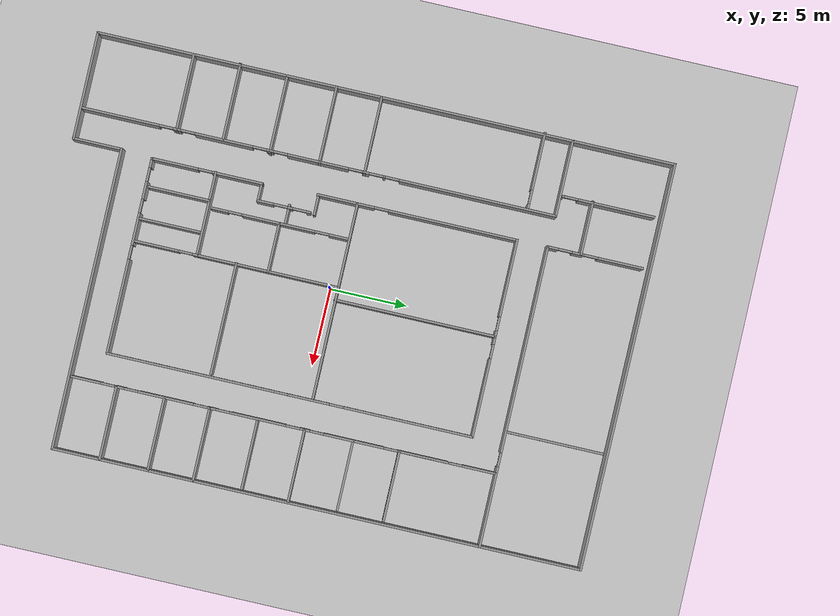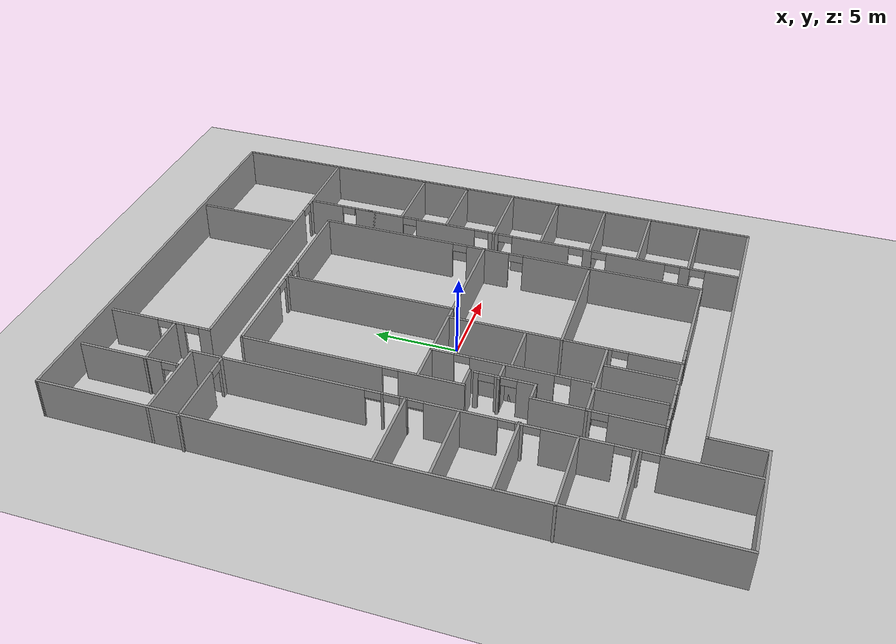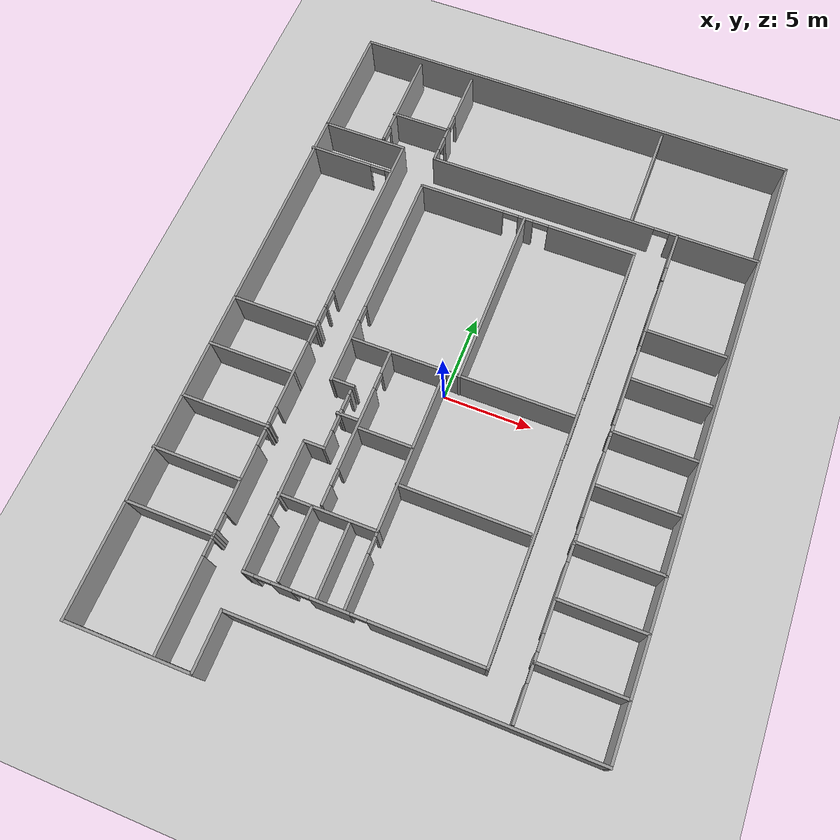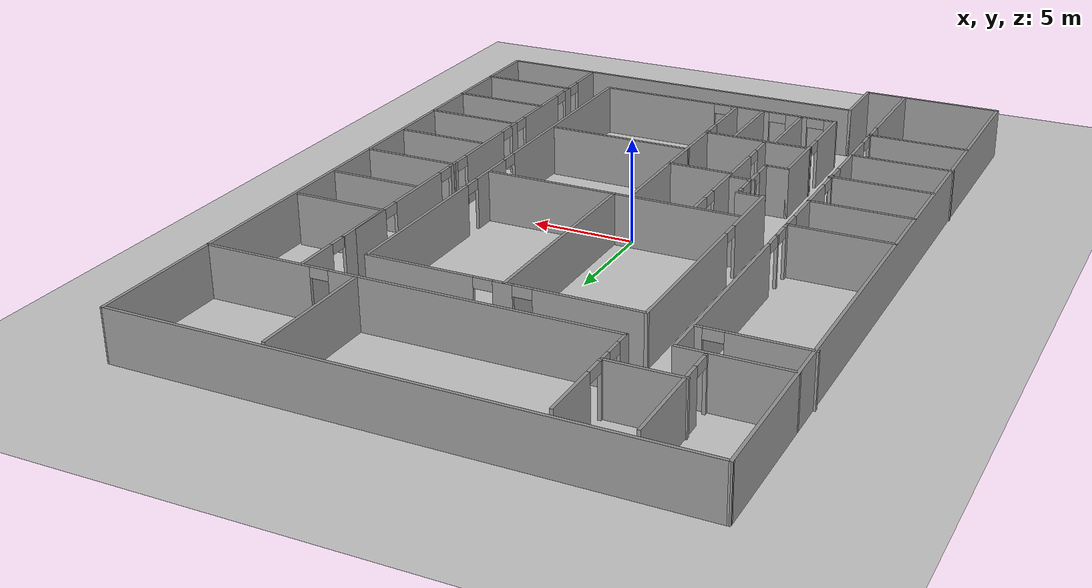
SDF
<sdf version="1.7">
 <world name="default">
  <plugin name="gazebo_octomap" filename="libBuildOctomapPlugin.so"/>
  <plugin name="gazebo_occupancy_map" filename="libgazebo_2dmap_plugin.so">
   <map_resolution>0.1</map_resolution>
   <map_height>0.3</map_height>
   <map_size_x>40</map_size_x>
   <map_size_y>40</map_size_y>
   <init_robot_x>-6.875570</init_robot_x>
   <init_robot_y>-13.324300</init_robot_y>
  </plugin>
  <light name="sun" type="directional">
   <pose>0 0 10 0 -0 0</pose>
   <diffuse>0.8 0.8 0.8 1</diffuse>
   <specular>0.2 0.2 0.2 1</specular>
   <attenuation>
    <range>1000</range>
    <constant>0.9</constant>
    <linear>0.01</linear>
    <quadratic>0.001</quadratic>
   </attenuation>
   <direction>-0.5 0.1 -0.9</direction>
   <spot><inner_angle>0</inner_angle><outer_angle>0</outer_angle><falloff>0</falloff></spot>
  </light>
  <model name="ground_plane">
   <static>1</static>
   <link name="link">
    <collision name="collision">
     <geometry><plane><normal>0 0 1</normal><size>100 100</size></plane></geometry>
     <surface><friction><ode><mu>100</mu><mu2>50</mu2></ode></friction></surface>
    </collision>
    <visual name="visual">
     <cast_shadows>0</cast_shadows>
     <geometry><plane><normal>0 0 1</normal><size>100 100</size></plane></geometry>
     <material>
      <script><uri>file://media/materials/scripts/gazebo.material</uri><name>Gazebo/Grey</name></script>
     </material>
    </visual>
   </link>
  </model>
  <gravity>0 0 -9.8</gravity>
  <magnetic_field>6e-06 2.3e-05 -4.2e-05</magnetic_field>
  <atmosphere type="adiabatic"/>
  <physics type="ode">
   <max_step_size>0.001</max_step_size>
   <real_time_factor>1</real_time_factor>
   <real_time_update_rate>1000</real_time_update_rate>
  </physics>
  <scene><ambient>0.4 0.4 0.4 1</ambient><background>0.7 0.7 0.7 1</background><shadows>1</shadows></scene>
  <spherical_coordinates>
   <surface_model>EARTH_WGS84</surface_model>
   <latitude_deg>0</latitude_deg>
   <longitude_deg>0</longitude_deg>
   <elevation>0</elevation>
   <heading_deg>0</heading_deg>
  </spherical_coordinates>
  <model name="GGB_1_floor">
   <pose>0.630572 -15.6046 0 0 -0 0</pose>
   <link name="Wall_0">
    <collision name="Wall_0_Collision">
     <geometry><box><size>37.5 0.15 2.5</size></box></geometry>
     <pose>0 0 1.25 0 -0 0</pose>
    </collision>
    <visual name="Wall_0_Visual">
     <pose>0 0 1.25 0 -0 0</pose>
     <geometry><box><size>37.5 0.15 2.5</size></box></geometry>
     <material>
      <script><uri>file://media/materials/scripts/gazebo.material</uri><name>Gazebo/Grey</name></script>
      <ambient>1 1 1 1</ambient>
     </material>
     <meta><layer>0</layer></meta>
    </visual>
    <pose>-13.0548 16.4245 0 0 -0 -1.5708</pose>
   </link>
   <link name="Wall_1">
    <collision name="Wall_1_Collision">
     <geometry><box><size>7 0.15 2.5</size></box></geometry>
     <pose>0 0 1.25 0 -0 0</pose>
    </collision>
    <visual name="Wall_1_Visual">
     <pose>0 0 1.25 0 -0 0</pose>
     <geometry><box><size>7 0.15 2.5</size></box></geometry>
     <material>
      <script><uri>file://media/materials/scripts/gazebo.material</uri><name>Gazebo/Grey</name></script>
      <ambient>1 1 1 1</ambient>
     </material>
     <meta><layer>0</layer></meta>
    </visual>
    <pose>-9.62976 -2.2505 0 0 -0 0</pose>
   </link>
   <link name="Wall_10">
    <pose>-8.20513 13.193 0 0 -0 -1.5708</pose>
    <visual name="Wall_10_Visual_0">
     <pose>-10.2751 0 1.25 0 -0 0</pose>
     <geometry><box><size>10.1998 0.15 2.5</size></box></geometry>
     <material>
      <script><uri>file://media/materials/scripts/gazebo.material</uri><name>Gazebo/Grey</name></script>
      <ambient>1 1 1 1</ambient>
     </material>
     <meta><layer>0</layer></meta>
    </visual>
    <collision name="Wall_10_Collision_0">
     <geometry><box><size>10.1998 0.15 2.5</size></box></geometry>
     <pose>-10.2751 0 1.25 0 -0 0</pose>
    </collision>
    <visual name="Wall_10_Visual_1">
     <pose>-4.20758 0 1.25 0 -0 0</pose>
     <geometry><box><size>0.135255 0.15 2.5</size></box></geometry>
     <material>
      <script><uri>file://media/materials/scripts/gazebo.material</uri><name>Gazebo/Grey</name></script>
      <ambient>1 1 1 1</ambient>
     </material>
     <meta><layer>0</layer></meta>
    </visual>
    <collision name="Wall_10_Collision_1">
     <geometry><box><size>0.135255 0.15 2.5</size></box></geometry>
     <pose>-4.20758 0 1.25 0 -0 0</pose>
    </collision>
    <visual name="Wall_10_Visual_2">
     <pose>-3.02117 0 1.25 0 -0 0</pose>
     <geometry><box><size>0.437563 0.15 2.5</size></box></geometry>
     <material>
      <script><uri>file://media/materials/scripts/gazebo.material</uri><name>Gazebo/Grey</name></script>
      <ambient>1 1 1 1</ambient>
     </material>
     <meta><layer>0</layer></meta>
    </visual>
    <collision name="Wall_10_Collision_2">
     <geometry><box><size>0.437563 0.15 2.5</size></box></geometry>
     <pose>-3.02117 0 1.25 0 -0 0</pose>
    </collision>
    <visual name="Wall_10_Visual_3">
     <pose>0.081968 0 1.25 0 -0 0</pose>
     <geometry><box><size>3.96873 0.15 2.5</size></box></geometry>
     <material>
      <script><uri>file://media/materials/scripts/gazebo.material</uri><name>Gazebo/Grey</name></script>
      <ambient>1 1 1 1</ambient>
     </material>
     <meta><layer>0</layer></meta>
    </visual>
    <collision name="Wall_10_Collision_3">
     <geometry><box><size>3.96873 0.15 2.5</size></box></geometry>
     <pose>0.081968 0 1.25 0 -0 0</pose>
    </collision>
    <visual name="Wall_10_Visual_4">
     <pose>3.18511 0 1.25 0 -0 0</pose>
     <geometry><box><size>0.437563 0.15 2.5</size></box></geometry>
     <material>
      <script><uri>file://media/materials/scripts/gazebo.material</uri><name>Gazebo/Grey</name></script>
      <ambient>1 1 1 1</ambient>
     </material>
     <meta><layer>0</layer></meta>
    </visual>
    <collision name="Wall_10_Collision_4">
     <geometry><box><size>0.437563 0.15 2.5</size></box></geometry>
     <pose>3.18511 0 1.25 0 -0 0</pose>
    </collision>
    <visual name="Wall_10_Visual_5">
     <pose>6.18125 0 1.25 0 -0 0</pose>
     <geometry><box><size>3.75472 0.15 2.5</size></box></geometry>
     <material>
      <script><uri>file://media/materials/scripts/gazebo.material</uri><name>Gazebo/Grey</name></script>
      <ambient>1 1 1 1</ambient>
     </material>
     <meta><layer>0</layer></meta>
    </visual>
    <collision name="Wall_10_Collision_5">
     <geometry><box><size>3.75472 0.15 2.5</size></box></geometry>
     <pose>6.18125 0 1.25 0 -0 0</pose>
    </collision>
    <visual name="Wall_10_Visual_6">
     <pose>9.20415 0 1.25 0 -0 0</pose>
     <geometry><box><size>0.491064 0.15 2.5</size></box></geometry>
     <material>
      <script><uri>file://media/materials/scripts/gazebo.material</uri><name>Gazebo/Grey</name></script>
      <ambient>1 1 1 1</ambient>
     </material>
     <meta><layer>0</layer></meta>
    </visual>
    <collision name="Wall_10_Collision_6">
     <geometry><box><size>0.491064 0.15 2.5</size></box></geometry>
     <pose>9.20415 0 1.25 0 -0 0</pose>
    </collision>
    <visual name="Wall_10_Visual_7">
     <pose>12.8623 0 1.25 0 -0 0</pose>
     <geometry><box><size>5.02532 0.15 2.5</size></box></geometry>
     <material>
      <script><uri>file://media/materials/scripts/gazebo.material</uri><name>Gazebo/Grey</name></script>
      <ambient>1 1 1 1</ambient>
     </material>
     <meta><layer>0</layer></meta>
    </visual>
    <collision name="Wall_10_Collision_7">
     <geometry><box><size>5.02532 0.15 2.5</size></box></geometry>
     <pose>12.8623 0 1.25 0 -0 0</pose>
    </collision>
    <visual name="Wall_10_Visual_8">
     <pose>-4.72521 0 2.25 0 -0 0</pose>
     <geometry><box><size>0.9 0.15 0.5</size></box></geometry>
     <material>
      <script><uri>file://media/materials/scripts/gazebo.material</uri><name>Gazebo/Grey</name></script>
      <ambient>1 1 1 1</ambient>
     </material>
     <meta><layer>0</layer></meta>
    </visual>
    <collision name="Wall_10_Collision_8">
     <geometry><box><size>0.9 0.15 0.5</size></box></geometry>
     <pose>-4.72521 0 2.25 0 -0 0</pose>
    </collision>
    <visual name="Wall_10_Visual_9">
     <pose>-3.68996 0 2.25 0 -0 0</pose>
     <geometry><box><size>0.9 0.15 0.5</size></box></geometry>
     <material>
      <script><uri>file://media/materials/scripts/gazebo.material</uri><name>Gazebo/Grey</name></script>
      <ambient>1 1 1 1</ambient>
     </material>
     <meta><layer>0</layer></meta>
    </visual>
    <collision name="Wall_10_Collision_9">
     <geometry><box><size>0.9 0.15 0.5</size></box></geometry>
     <pose>-3.68996 0 2.25 0 -0 0</pose>
    </collision>
    <visual name="Wall_10_Visual_10">
     <pose>-2.35239 0 2.25 0 -0 0</pose>
     <geometry><box><size>0.9 0.15 0.5</size></box></geometry>
     <material>
      <script><uri>file://media/materials/scripts/gazebo.material</uri><name>Gazebo/Grey</name></script>
      <ambient>1 1 1 1</ambient>
     </material>
     <meta><layer>0</layer></meta>
    </visual>
    <collision name="Wall_10_Collision_10">
     <geometry><box><size>0.9 0.15 0.5</size></box></geometry>
     <pose>-2.35239 0 2.25 0 -0 0</pose>
    </collision>
    <visual name="Wall_10_Visual_11">
     <pose>2.51633 0 2.25 0 -0 0</pose>
     <geometry><box><size>0.9 0.15 0.5</size></box></geometry>
     <material>
      <script><uri>file://media/materials/scripts/gazebo.material</uri><name>Gazebo/Grey</name></script>
      <ambient>1 1 1 1</ambient>
     </material>
     <meta><layer>0</layer></meta>
    </visual>
    <collision name="Wall_10_Collision_11">
     <geometry><box><size>0.9 0.15 0.5</size></box></geometry>
     <pose>2.51633 0 2.25 0 -0 0</pose>
    </collision>
    <visual name="Wall_10_Visual_12">
     <pose>3.85389 0 2.25 0 -0 0</pose>
     <geometry><box><size>0.9 0.15 0.5</size></box></geometry>
     <material>
      <script><uri>file://media/materials/scripts/gazebo.material</uri><name>Gazebo/Grey</name></script>
      <ambient>1 1 1 1</ambient>
     </material>
     <meta><layer>0</layer></meta>
    </visual>
    <collision name="Wall_10_Collision_12">
     <geometry><box><size>0.9 0.15 0.5</size></box></geometry>
     <pose>3.85389 0 2.25 0 -0 0</pose>
    </collision>
    <visual name="Wall_10_Visual_13">
     <pose>8.50861 0 2.25 0 -0 0</pose>
     <geometry><box><size>0.9 0.15 0.5</size></box></geometry>
     <material>
      <script><uri>file://media/materials/scripts/gazebo.material</uri><name>Gazebo/Grey</name></script>
      <ambient>1 1 1 1</ambient>
     </material>
     <meta><layer>0</layer></meta>
    </visual>
    <collision name="Wall_10_Collision_13">
     <geometry><box><size>0.9 0.15 0.5</size></box></geometry>
     <pose>8.50861 0 2.25 0 -0 0</pose>
    </collision>
    <visual name="Wall_10_Visual_14">
     <pose>9.89968 0 2.25 0 -0 0</pose>
     <geometry><box><size>0.9 0.15 0.5</size></box></geometry>
     <material>
      <script><uri>file://media/materials/scripts/gazebo.material</uri><name>Gazebo/Grey</name></script>
      <ambient>1 1 1 1</ambient>
     </material>
     <meta><layer>0</layer></meta>
    </visual>
    <collision name="Wall_10_Collision_14">
     <geometry><box><size>0.9 0.15 0.5</size></box></geometry>
     <pose>9.89968 0 2.25 0 -0 0</pose>
    </collision>
   </link>
   <link name="Wall_12">
    <pose>-6.20681 31.4888 0 0 -0 -1.5708</pose>
    <visual name="Wall_12_Visual_0">
     <pose>-1.65393 0 1.25 0 -0 0</pose>
     <geometry><box><size>2.94215 0.15 2.5</size></box></geometry>
     <material>
      <script><uri>file://media/materials/scripts/gazebo.material</uri><name>Gazebo/Grey</name></script>
      <ambient>1 1 1 1</ambient>
     </material>
     <meta><layer>0</layer></meta>
    </visual>
    <collision name="Wall_12_Collision_0">
     <geometry><box><size>2.94215 0.15 2.5</size></box></geometry>
     <pose>-1.65393 0 1.25 0 -0 0</pose>
    </collision>
    <visual name="Wall_12_Visual_1">
     <pose>1.09644 0 1.25 0 -0 0</pose>
     <geometry><box><size>0.758577 0.15 2.5</size></box></geometry>
     <material>
      <script><uri>file://media/materials/scripts/gazebo.material</uri><name>Gazebo/Grey</name></script>
      <ambient>1 1 1 1</ambient>
     </material>
     <meta><layer>0</layer></meta>
    </visual>
    <collision name="Wall_12_Collision_1">
     <geometry><box><size>0.758577 0.15 2.5</size></box></geometry>
     <pose>1.09644 0 1.25 0 -0 0</pose>
    </collision>
    <visual name="Wall_12_Visual_2">
     <pose>2.75036 0 1.25 0 -0 0</pose>
     <geometry><box><size>0.749272 0.15 2.5</size></box></geometry>
     <material>
      <script><uri>file://media/materials/scripts/gazebo.material</uri><name>Gazebo/Grey</name></script>
      <ambient>1 1 1 1</ambient>
     </material>
     <meta><layer>0</layer></meta>
    </visual>
    <collision name="Wall_12_Collision_2">
     <geometry><box><size>0.749272 0.15 2.5</size></box></geometry>
     <pose>2.75036 0 1.25 0 -0 0</pose>
    </collision>
    <visual name="Wall_12_Visual_3">
     <pose>0.267151 0 2.25 0 -0 0</pose>
     <geometry><box><size>0.9 0.15 0.5</size></box></geometry>
     <material>
      <script><uri>file://media/materials/scripts/gazebo.material</uri><name>Gazebo/Grey</name></script>
      <ambient>1 1 1 1</ambient>
     </material>
     <meta><layer>0</layer></meta>
    </visual>
    <collision name="Wall_12_Collision_3">
     <geometry><box><size>0.9 0.15 0.5</size></box></geometry>
     <pose>0.267151 0 2.25 0 -0 0</pose>
    </collision>
    <visual name="Wall_12_Visual_4">
     <pose>1.92573 0 2.25 0 -0 0</pose>
     <geometry><box><size>0.9 0.15 0.5</size></box></geometry>
     <material>
      <script><uri>file://media/materials/scripts/gazebo.material</uri><name>Gazebo/Grey</name></script>
      <ambient>1 1 1 1</ambient>
     </material>
     <meta><layer>0</layer></meta>
    </visual>
    <collision name="Wall_12_Collision_4">
     <geometry><box><size>0.9 0.15 0.5</size></box></geometry>
     <pose>1.92573 0 2.25 0 -0 0</pose>
    </collision>
   </link>
   <link name="Wall_13">
    <pose>3.46819 28.4388 0 0 -0 0</pose>
    <visual name="Wall_13_Visual_0">
     <pose>-3.06133 0 1.25 0 -0 0</pose>
     <geometry><box><size>13.3773 0.15 2.5</size></box></geometry>
     <material>
      <script><uri>file://media/materials/scripts/gazebo.material</uri><name>Gazebo/Grey</name></script>
      <ambient>1 1 1 1</ambient>
     </material>
     <meta><layer>0</layer></meta>
    </visual>
    <collision name="Wall_13_Collision_0">
     <geometry><box><size>13.3773 0.15 2.5</size></box></geometry>
     <pose>-3.06133 0 1.25 0 -0 0</pose>
    </collision>
    <visual name="Wall_13_Visual_1">
     <pose>7.13867 0 1.25 0 -0 0</pose>
     <geometry><box><size>5.22265 0.15 2.5</size></box></geometry>
     <material>
      <script><uri>file://media/materials/scripts/gazebo.material</uri><name>Gazebo/Grey</name></script>
      <ambient>1 1 1 1</ambient>
     </material>
     <meta><layer>0</layer></meta>
    </visual>
    <collision name="Wall_13_Collision_1">
     <geometry><box><size>5.22265 0.15 2.5</size></box></geometry>
     <pose>7.13867 0 1.25 0 -0 0</pose>
    </collision>
    <visual name="Wall_13_Visual_2">
     <pose>4.07735 0 2.25 0 -0 0</pose>
     <geometry><box><size>0.9 0.15 0.5</size></box></geometry>
     <material>
      <script><uri>file://media/materials/scripts/gazebo.material</uri><name>Gazebo/Grey</name></script>
      <ambient>1 1 1 1</ambient>
     </material>
     <meta><layer>0</layer></meta>
    </visual>
    <collision name="Wall_13_Collision_2">
     <geometry><box><size>0.9 0.15 0.5</size></box></geometry>
     <pose>4.07735 0 2.25 0 -0 0</pose>
    </collision>
   </link>
   <link name="Wall_15">
    <pose>8.45287 14.711 0 0 -0 -1.5708</pose>
    <visual name="Wall_15_Visual_0">
     <pose>-12.6394 0 1.25 0 -0 0</pose>
     <geometry><box><size>2.22115 0.15 2.5</size></box></geometry>
     <material>
      <script><uri>file://media/materials/scripts/gazebo.material</uri><name>Gazebo/Grey</name></script>
      <ambient>1 1 1 1</ambient>
     </material>
     <meta><layer>0</layer></meta>
    </visual>
    <collision name="Wall_15_Collision_0">
     <geometry><box><size>2.22115 0.15 2.5</size></box></geometry>
     <pose>-12.6394 0 1.25 0 -0 0</pose>
    </collision>
    <visual name="Wall_15_Visual_1">
     <pose>-9.0033 0 1.25 0 -0 0</pose>
     <geometry><box><size>3.25109 0.15 2.5</size></box></geometry>
     <material>
      <script><uri>file://media/materials/scripts/gazebo.material</uri><name>Gazebo/Grey</name></script>
      <ambient>1 1 1 1</ambient>
     </material>
     <meta><layer>0</layer></meta>
    </visual>
    <collision name="Wall_15_Collision_1">
     <geometry><box><size>3.25109 0.15 2.5</size></box></geometry>
     <pose>-9.0033 0 1.25 0 -0 0</pose>
    </collision>
    <visual name="Wall_15_Visual_2">
     <pose>-8.58115 0 1.25 0 -0 0</pose>
     <geometry><box><size>2.4068 0.15 2.5</size></box></geometry>
     <material>
      <script><uri>file://media/materials/scripts/gazebo.material</uri><name>Gazebo/Grey</name></script>
      <ambient>1 1 1 1</ambient>
     </material>
     <meta><layer>0</layer></meta>
    </visual>
    <collision name="Wall_15_Collision_2">
     <geometry><box><size>2.4068 0.15 2.5</size></box></geometry>
     <pose>-8.58115 0 1.25 0 -0 0</pose>
    </collision>
    <visual name="Wall_15_Visual_3">
     <pose>-4.5356 0 1.25 0 -0 0</pose>
     <geometry><box><size>3.88431 0.15 2.5</size></box></geometry>
     <material>
      <script><uri>file://media/materials/scripts/gazebo.material</uri><name>Gazebo/Grey</name></script>
      <ambient>1 1 1 1</ambient>
     </material>
     <meta><layer>0</layer></meta>
    </visual>
    <collision name="Wall_15_Collision_3">
     <geometry><box><size>3.88431 0.15 2.5</size></box></geometry>
     <pose>-4.5356 0 1.25 0 -0 0</pose>
    </collision>
    <visual name="Wall_15_Visual_4">
     <pose>-1.36951 0 1.25 0 -0 0</pose>
     <geometry><box><size>0.647867 0.15 2.5</size></box></geometry>
     <material>
      <script><uri>file://media/materials/scripts/gazebo.material</uri><name>Gazebo/Grey</name></script>
      <ambient>1 1 1 1</ambient>
     </material>
     <meta><layer>0</layer></meta>
    </visual>
    <collision name="Wall_15_Collision_4">
     <geometry><box><size>0.647867 0.15 2.5</size></box></geometry>
     <pose>-1.36951 0 1.25 0 -0 0</pose>
    </collision>
    <visual name="Wall_15_Visual_5">
     <pose>1.66587 0 1.25 0 -0 0</pose>
     <geometry><box><size>3.6229 0.15 2.5</size></box></geometry>
     <material>
      <script><uri>file://media/materials/scripts/gazebo.material</uri><name>Gazebo/Grey</name></script>
      <ambient>1 1 1 1</ambient>
     </material>
     <meta><layer>0</layer></meta>
    </visual>
    <collision name="Wall_15_Collision_5">
     <geometry><box><size>3.6229 0.15 2.5</size></box></geometry>
     <pose>1.66587 0 1.25 0 -0 0</pose>
    </collision>
    <visual name="Wall_15_Visual_6">
     <pose>4.64961 0 1.25 0 -0 0</pose>
     <geometry><box><size>0.544565 0.15 2.5</size></box></geometry>
     <material>
      <script><uri>file://media/materials/scripts/gazebo.material</uri><name>Gazebo/Grey</name></script>
      <ambient>1 1 1 1</ambient>
     </material>
     <meta><layer>0</layer></meta>
    </visual>
    <collision name="Wall_15_Collision_6">
     <geometry><box><size>0.544565 0.15 2.5</size></box></geometry>
     <pose>4.64961 0 1.25 0 -0 0</pose>
    </collision>
    <visual name="Wall_15_Visual_7">
     <pose>7.61899 0 1.25 0 -0 0</pose>
     <geometry><box><size>3.59421 0.15 2.5</size></box></geometry>
     <material>
      <script><uri>file://media/materials/scripts/gazebo.material</uri><name>Gazebo/Grey</name></script>
      <ambient>1 1 1 1</ambient>
     </material>
     <meta><layer>0</layer></meta>
    </visual>
    <collision name="Wall_15_Collision_7">
     <geometry><box><size>3.59421 0.15 2.5</size></box></geometry>
     <pose>7.61899 0 1.25 0 -0 0</pose>
    </collision>
    <visual name="Wall_15_Visual_8">
     <pose>10.6151 0 1.25 0 -0 0</pose>
     <geometry><box><size>0.59807 0.15 2.5</size></box></geometry>
     <material>
      <script><uri>file://media/materials/scripts/gazebo.material</uri><name>Gazebo/Grey</name></script>
      <ambient>1 1 1 1</ambient>
     </material>
     <meta><layer>0</layer></meta>
    </visual>
    <collision name="Wall_15_Collision_8">
     <geometry><box><size>0.59807 0.15 2.5</size></box></geometry>
     <pose>10.6151 0 1.25 0 -0 0</pose>
    </collision>
    <visual name="Wall_15_Visual_9">
     <pose>12.7821 0 1.25 0 -0 0</pose>
     <geometry><box><size>1.93583 0.15 2.5</size></box></geometry>
     <material>
      <script><uri>file://media/materials/scripts/gazebo.material</uri><name>Gazebo/Grey</name></script>
      <ambient>1 1 1 1</ambient>
     </material>
     <meta><layer>0</layer></meta>
    </visual>
    <collision name="Wall_15_Collision_9">
     <geometry><box><size>1.93583 0.15 2.5</size></box></geometry>
     <pose>12.7821 0 1.25 0 -0 0</pose>
    </collision>
    <visual name="Wall_15_Visual_10">
     <pose>-11.1067 0 2.25 0 -0 0</pose>
     <geometry><box><size>0.844292 0.15 0.5</size></box></geometry>
     <material>
      <script><uri>file://media/materials/scripts/gazebo.material</uri><name>Gazebo/Grey</name></script>
      <ambient>1 1 1 1</ambient>
     </material>
     <meta><layer>0</layer></meta>
    </visual>
    <collision name="Wall_15_Collision_10">
     <geometry><box><size>0.844292 0.15 0.5</size></box></geometry>
     <pose>-11.1067 0 2.25 0 -0 0</pose>
    </collision>
    <visual name="Wall_15_Visual_11">
     <pose>-6.92775 0 2.25 0 -0 0</pose>
     <geometry><box><size>0.9 0.15 0.5</size></box></geometry>
     <material>
      <script><uri>file://media/materials/scripts/gazebo.material</uri><name>Gazebo/Grey</name></script>
      <ambient>1 1 1 1</ambient>
     </material>
     <meta><layer>0</layer></meta>
    </visual>
    <collision name="Wall_15_Collision_11">
     <geometry><box><size>0.9 0.15 0.5</size></box></geometry>
     <pose>-6.92775 0 2.25 0 -0 0</pose>
    </collision>
    <visual name="Wall_15_Visual_12">
     <pose>-6.92775 0 2.25 0 -0 0</pose>
     <geometry><box><size>0.9 0.15 0.5</size></box></geometry>
     <material>
      <script><uri>file://media/materials/scripts/gazebo.material</uri><name>Gazebo/Grey</name></script>
      <ambient>1 1 1 1</ambient>
     </material>
     <meta><layer>0</layer></meta>
    </visual>
    <collision name="Wall_15_Collision_12">
     <geometry><box><size>0.9 0.15 0.5</size></box></geometry>
     <pose>-6.92775 0 2.25 0 -0 0</pose>
    </collision>
    <visual name="Wall_15_Visual_13">
     <pose>-2.14344 0 2.25 0 -0 0</pose>
     <geometry><box><size>0.9 0.15 0.5</size></box></geometry>
     <material>
      <script><uri>file://media/materials/scripts/gazebo.material</uri><name>Gazebo/Grey</name></script>
      <ambient>1 1 1 1</ambient>
     </material>
     <meta><layer>0</layer></meta>
    </visual>
    <collision name="Wall_15_Collision_13">
     <geometry><box><size>0.9 0.15 0.5</size></box></geometry>
     <pose>-2.14344 0 2.25 0 -0 0</pose>
    </collision>
    <visual name="Wall_15_Visual_14">
     <pose>-0.595573 0 2.25 0 -0 0</pose>
     <geometry><box><size>0.9 0.15 0.5</size></box></geometry>
     <material>
      <script><uri>file://media/materials/scripts/gazebo.material</uri><name>Gazebo/Grey</name></script>
      <ambient>1 1 1 1</ambient>
     </material>
     <meta><layer>0</layer></meta>
    </visual>
    <collision name="Wall_15_Collision_14">
     <geometry><box><size>0.9 0.15 0.5</size></box></geometry>
     <pose>-0.595573 0 2.25 0 -0 0</pose>
    </collision>
    <visual name="Wall_15_Visual_15">
     <pose>3.92732 0 2.25 0 -0 0</pose>
     <geometry><box><size>0.9 0.15 0.5</size></box></geometry>
     <material>
      <script><uri>file://media/materials/scripts/gazebo.material</uri><name>Gazebo/Grey</name></script>
      <ambient>1 1 1 1</ambient>
     </material>
     <meta><layer>0</layer></meta>
    </visual>
    <collision name="Wall_15_Collision_15">
     <geometry><box><size>0.9 0.15 0.5</size></box></geometry>
     <pose>3.92732 0 2.25 0 -0 0</pose>
    </collision>
    <visual name="Wall_15_Visual_16">
     <pose>5.37189 0 2.25 0 -0 0</pose>
     <geometry><box><size>0.9 0.15 0.5</size></box></geometry>
     <material>
      <script><uri>file://media/materials/scripts/gazebo.material</uri><name>Gazebo/Grey</name></script>
      <ambient>1 1 1 1</ambient>
     </material>
     <meta><layer>0</layer></meta>
    </visual>
    <collision name="Wall_15_Collision_16">
     <geometry><box><size>0.9 0.15 0.5</size></box></geometry>
     <pose>5.37189 0 2.25 0 -0 0</pose>
    </collision>
    <visual name="Wall_15_Visual_17">
     <pose>9.8661 0 2.25 0 -0 0</pose>
     <geometry><box><size>0.9 0.15 0.5</size></box></geometry>
     <material>
      <script><uri>file://media/materials/scripts/gazebo.material</uri><name>Gazebo/Grey</name></script>
      <ambient>1 1 1 1</ambient>
     </material>
     <meta><layer>0</layer></meta>
    </visual>
    <collision name="Wall_15_Collision_17">
     <geometry><box><size>0.9 0.15 0.5</size></box></geometry>
     <pose>9.8661 0 2.25 0 -0 0</pose>
    </collision>
    <visual name="Wall_15_Visual_18">
     <pose>11.3642 0 2.25 0 -0 0</pose>
     <geometry><box><size>0.9 0.15 0.5</size></box></geometry>
     <material>
      <script><uri>file://media/materials/scripts/gazebo.material</uri><name>Gazebo/Grey</name></script>
      <ambient>1 1 1 1</ambient>
     </material>
     <meta><layer>0</layer></meta>
    </visual>
    <collision name="Wall_15_Collision_18">
     <geometry><box><size>0.9 0.15 0.5</size></box></geometry>
     <pose>11.3642 0 2.25 0 -0 0</pose>
    </collision>
   </link>
   <link name="Wall_17">
    <pose>0.180575 26.4599 0 0 -0 0</pose>
    <visual name="Wall_17_Visual_0">
     <pose>-3.91897 0 1.25 0 -0 0</pose>
     <geometry><box><size>5.02336 0.15 2.5</size></box></geometry>
     <material>
      <script><uri>file://media/materials/scripts/gazebo.material</uri><name>Gazebo/Grey</name></script>
      <ambient>1 1 1 1</ambient>
     </material>
     <meta><layer>0</layer></meta>
    </visual>
    <collision name="Wall_17_Collision_0">
     <geometry><box><size>5.02336 0.15 2.5</size></box></geometry>
     <pose>-3.91897 0 1.25 0 -0 0</pose>
    </collision>
    <visual name="Wall_17_Visual_1">
     <pose>-0.057574 0 1.25 0 -0 0</pose>
     <geometry><box><size>0.899438 0.15 2.5</size></box></geometry>
     <material>
      <script><uri>file://media/materials/scripts/gazebo.material</uri><name>Gazebo/Grey</name></script>
      <ambient>1 1 1 1</ambient>
     </material>
     <meta><layer>0</layer></meta>
    </visual>
    <collision name="Wall_17_Collision_1">
     <geometry><box><size>0.899438 0.15 2.5</size></box></geometry>
     <pose>-0.057574 0 1.25 0 -0 0</pose>
    </collision>
    <visual name="Wall_17_Visual_2">
     <pose>3.8614 0 1.25 0 -0 0</pose>
     <geometry><box><size>5.13851 0.15 2.5</size></box></geometry>
     <material>
      <script><uri>file://media/materials/scripts/gazebo.material</uri><name>Gazebo/Grey</name></script>
      <ambient>1 1 1 1</ambient>
     </material>
     <meta><layer>0</layer></meta>
    </visual>
    <collision name="Wall_17_Collision_2">
     <geometry><box><size>5.13851 0.15 2.5</size></box></geometry>
     <pose>3.8614 0 1.25 0 -0 0</pose>
    </collision>
    <visual name="Wall_17_Visual_3">
     <pose>-0.957293 0 2.25 0 -0 0</pose>
     <geometry><box><size>0.9 0.15 0.5</size></box></geometry>
     <material>
      <script><uri>file://media/materials/scripts/gazebo.material</uri><name>Gazebo/Grey</name></script>
      <ambient>1 1 1 1</ambient>
     </material>
     <meta><layer>0</layer></meta>
    </visual>
    <collision name="Wall_17_Collision_3">
     <geometry><box><size>0.9 0.15 0.5</size></box></geometry>
     <pose>-0.957293 0 2.25 0 -0 0</pose>
    </collision>
    <visual name="Wall_17_Visual_4">
     <pose>0.842145 0 2.25 0 -0 0</pose>
     <geometry><box><size>0.9 0.15 0.5</size></box></geometry>
     <material>
      <script><uri>file://media/materials/scripts/gazebo.material</uri><name>Gazebo/Grey</name></script>
      <ambient>1 1 1 1</ambient>
     </material>
     <meta><layer>0</layer></meta>
    </visual>
    <collision name="Wall_17_Collision_4">
     <geometry><box><size>0.9 0.15 0.5</size></box></geometry>
     <pose>0.842145 0 2.25 0 -0 0</pose>
    </collision>
   </link>
   <link name="Wall_18">
    <pose>6.53618 14.6599 0 0 -0 -1.5708</pose>
    <visual name="Wall_18_Visual_0">
     <pose>-7.67529 0 1.25 0 -0 0</pose>
     <geometry><box><size>8.39941 0.15 2.5</size></box></geometry>
     <material>
      <script><uri>file://media/materials/scripts/gazebo.material</uri><name>Gazebo/Grey</name></script>
      <ambient>1 1 1 1</ambient>
     </material>
     <meta><layer>0</layer></meta>
    </visual>
    <collision name="Wall_18_Collision_0">
     <geometry><box><size>8.39941 0.15 2.5</size></box></geometry>
     <pose>-7.67529 0 1.25 0 -0 0</pose>
    </collision>
    <visual name="Wall_18_Visual_1">
     <pose>-1.23325 0 1.25 0 -0 0</pose>
     <geometry><box><size>2.68467 0.15 2.5</size></box></geometry>
     <material>
      <script><uri>file://media/materials/scripts/gazebo.material</uri><name>Gazebo/Grey</name></script>
      <ambient>1 1 1 1</ambient>
     </material>
     <meta><layer>0</layer></meta>
    </visual>
    <collision name="Wall_18_Collision_1">
     <geometry><box><size>2.68467 0.15 2.5</size></box></geometry>
     <pose>-1.23325 0 1.25 0 -0 0</pose>
    </collision>
    <visual name="Wall_18_Visual_2">
     <pose>6.44204 0 1.25 0 -0 0</pose>
     <geometry><box><size>10.8659 0.15 2.5</size></box></geometry>
     <material>
      <script><uri>file://media/materials/scripts/gazebo.material</uri><name>Gazebo/Grey</name></script>
      <ambient>1 1 1 1</ambient>
     </material>
     <meta><layer>0</layer></meta>
    </visual>
    <collision name="Wall_18_Collision_2">
     <geometry><box><size>10.8659 0.15 2.5</size></box></geometry>
     <pose>6.44204 0 1.25 0 -0 0</pose>
    </collision>
    <visual name="Wall_18_Visual_3">
     <pose>-3.02559 0 2.25 0 -0 0</pose>
     <geometry><box><size>0.9 0.15 0.5</size></box></geometry>
     <material>
      <script><uri>file://media/materials/scripts/gazebo.material</uri><name>Gazebo/Grey</name></script>
      <ambient>1 1 1 1</ambient>
     </material>
     <meta><layer>0</layer></meta>
    </visual>
    <collision name="Wall_18_Collision_3">
     <geometry><box><size>0.9 0.15 0.5</size></box></geometry>
     <pose>-3.02559 0 2.25 0 -0 0</pose>
    </collision>
    <visual name="Wall_18_Visual_4">
     <pose>0.559078 0 2.25 0 -0 0</pose>
     <geometry><box><size>0.9 0.15 0.5</size></box></geometry>
     <material>
      <script><uri>file://media/materials/scripts/gazebo.material</uri><name>Gazebo/Grey</name></script>
      <ambient>1 1 1 1</ambient>
     </material>
     <meta><layer>0</layer></meta>
    </visual>
    <collision name="Wall_18_Collision_4">
     <geometry><box><size>0.9 0.15 0.5</size></box></geometry>
     <pose>0.559078 0 2.25 0 -0 0</pose>
    </collision>
   </link>
   <link name="Wall_19">
    <pose>0.236183 2.85993 0 0 -0 3.14159</pose>
    <visual name="Wall_19_Visual_0">
     <pose>-3.29415 0 1.25 0 -0 0</pose>
     <geometry><box><size>6.16171 0.15 2.5</size></box></geometry>
     <material>
      <script><uri>file://media/materials/scripts/gazebo.material</uri><name>Gazebo/Grey</name></script>
      <ambient>1 1 1 1</ambient>
     </material>
     <meta><layer>0</layer></meta>
    </visual>
    <collision name="Wall_19_Collision_0">
     <geometry><box><size>6.16171 0.15 2.5</size></box></geometry>
     <pose>-3.29415 0 1.25 0 -0 0</pose>
    </collision>
    <visual name="Wall_19_Visual_1">
     <pose>1.73477 0 1.25 0 -0 0</pose>
     <geometry><box><size>2.09614 0.15 2.5</size></box></geometry>
     <material>
      <script><uri>file://media/materials/scripts/gazebo.material</uri><name>Gazebo/Grey</name></script>
      <ambient>1 1 1 1</ambient>
     </material>
     <meta><layer>0</layer></meta>
    </visual>
    <collision name="Wall_19_Collision_1">
     <geometry><box><size>2.09614 0.15 2.5</size></box></geometry>
     <pose>1.73477 0 1.25 0 -0 0</pose>
    </collision>
    <visual name="Wall_19_Visual_2">
     <pose>4.24939 0 1.25 0 -0 0</pose>
     <geometry><box><size>1.13309 0.15 2.5</size></box></geometry>
     <material>
      <script><uri>file://media/materials/scripts/gazebo.material</uri><name>Gazebo/Grey</name></script>
      <ambient>1 1 1 1</ambient>
     </material>
     <meta><layer>0</layer></meta>
    </visual>
    <collision name="Wall_19_Collision_2">
     <geometry><box><size>1.13309 0.15 2.5</size></box></geometry>
     <pose>4.24939 0 1.25 0 -0 0</pose>
    </collision>
    <visual name="Wall_19_Visual_3">
     <pose>6.04547 0 1.25 0 -0 0</pose>
     <geometry><box><size>0.65906 0.15 2.5</size></box></geometry>
     <material>
      <script><uri>file://media/materials/scripts/gazebo.material</uri><name>Gazebo/Grey</name></script>
      <ambient>1 1 1 1</ambient>
     </material>
     <meta><layer>0</layer></meta>
    </visual>
    <collision name="Wall_19_Collision_3">
     <geometry><box><size>0.65906 0.15 2.5</size></box></geometry>
     <pose>6.04547 0 1.25 0 -0 0</pose>
    </collision>
    <visual name="Wall_19_Visual_4">
     <pose>0.236705 0 2.25 0 -0 0</pose>
     <geometry><box><size>0.9 0.15 0.5</size></box></geometry>
     <material>
      <script><uri>file://media/materials/scripts/gazebo.material</uri><name>Gazebo/Grey</name></script>
      <ambient>1 1 1 1</ambient>
     </material>
     <meta><layer>0</layer></meta>
    </visual>
    <collision name="Wall_19_Collision_4">
     <geometry><box><size>0.9 0.15 0.5</size></box></geometry>
     <pose>0.236705 0 2.25 0 -0 0</pose>
    </collision>
    <visual name="Wall_19_Visual_5">
     <pose>3.23284 0 2.25 0 -0 0</pose>
     <geometry><box><size>0.9 0.15 0.5</size></box></geometry>
     <material>
      <script><uri>file://media/materials/scripts/gazebo.material</uri><name>Gazebo/Grey</name></script>
      <ambient>1 1 1 1</ambient>
     </material>
     <meta><layer>0</layer></meta>
    </visual>
    <collision name="Wall_19_Collision_5">
     <geometry><box><size>0.9 0.15 0.5</size></box></geometry>
     <pose>3.23284 0 2.25 0 -0 0</pose>
    </collision>
    <visual name="Wall_19_Visual_6">
     <pose>5.26594 0 2.25 0 -0 0</pose>
     <geometry><box><size>0.9 0.15 0.5</size></box></geometry>
     <material>
      <script><uri>file://media/materials/scripts/gazebo.material</uri><name>Gazebo/Grey</name></script>
      <ambient>1 1 1 1</ambient>
     </material>
     <meta><layer>0</layer></meta>
    </visual>
    <collision name="Wall_19_Collision_6">
     <geometry><box><size>0.9 0.15 0.5</size></box></geometry>
     <pose>5.26594 0 2.25 0 -0 0</pose>
    </collision>
   </link>
   <link name="Wall_2">
    <collision name="Wall_2_Collision">
     <geometry><box><size>3.25 0.15 2.5</size></box></geometry>
     <pose>0 0 1.25 0 -0 0</pose>
    </collision>
    <visual name="Wall_2_Visual">
     <pose>0 0 1.25 0 -0 0</pose>
     <geometry><box><size>3.25 0.15 2.5</size></box></geometry>
     <material>
      <script><uri>file://media/materials/scripts/gazebo.material</uri><name>Gazebo/Grey</name></script>
      <ambient>1 1 1 1</ambient>
     </material>
     <meta><layer>0</layer></meta>
    </visual>
    <pose>-6.20476 -0.700497 0 0 -0 1.5708</pose>
   </link>
   <link name="Wall_20">
    <pose>-6.06382 6.40993 0 0 -0 1.5708</pose>
    <visual name="Wall_20_Visual_0">
     <pose>-2.09772 0 1.25 0 -0 0</pose>
     <geometry><box><size>3.05456 0.15 2.5</size></box></geometry>
     <material>
      <script><uri>file://media/materials/scripts/gazebo.material</uri><name>Gazebo/Grey</name></script>
      <ambient>1 1 1 1</ambient>
     </material>
     <meta><layer>0</layer></meta>
    </visual>
    <collision name="Wall_20_Collision_0">
     <geometry><box><size>3.05456 0.15 2.5</size></box></geometry>
     <pose>-2.09772 0 1.25 0 -0 0</pose>
    </collision>
    <visual name="Wall_20_Visual_1">
     <pose>1.97728 0 1.25 0 -0 0</pose>
     <geometry><box><size>3.29544 0.15 2.5</size></box></geometry>
     <material>
      <script><uri>file://media/materials/scripts/gazebo.material</uri><name>Gazebo/Grey</name></script>
      <ambient>1 1 1 1</ambient>
     </material>
     <meta><layer>0</layer></meta>
    </visual>
    <collision name="Wall_20_Collision_1">
     <geometry><box><size>3.29544 0.15 2.5</size></box></geometry>
     <pose>1.97728 0 1.25 0 -0 0</pose>
    </collision>
    <visual name="Wall_20_Visual_2">
     <pose>-0.120445 0 2.25 0 -0 0</pose>
     <geometry><box><size>0.9 0.15 0.5</size></box></geometry>
     <material>
      <script><uri>file://media/materials/scripts/gazebo.material</uri><name>Gazebo/Grey</name></script>
      <ambient>1 1 1 1</ambient>
     </material>
     <meta><layer>0</layer></meta>
    </visual>
    <collision name="Wall_20_Collision_2">
     <geometry><box><size>0.9 0.15 0.5</size></box></geometry>
     <pose>-0.120445 0 2.25 0 -0 0</pose>
    </collision>
   </link>
   <link name="Wall_21">
    <collision name="Wall_21_Collision">
     <geometry><box><size>1.25 0.15 2.5</size></box></geometry>
     <pose>0 0 1.25 0 -0 0</pose>
    </collision>
    <visual name="Wall_21_Visual">
     <pose>0 0 1.25 0 -0 0</pose>
     <geometry><box><size>1.25 0.15 2.5</size></box></geometry>
     <material>
      <script><uri>file://media/materials/scripts/gazebo.material</uri><name>Gazebo/Grey</name></script>
      <ambient>1 1 1 1</ambient>
     </material>
     <meta><layer>0</layer></meta>
    </visual>
    <pose>-5.51382 9.95993 0 0 -0 0</pose>
   </link>
   <link name="Wall_22">
    <pose>-4.96382 11.6349 0 0 -0 1.5708</pose>
    <visual name="Wall_22_Visual_0">
     <pose>-1.2046 0 1.25 0 -0 0</pose>
     <geometry><box><size>1.0908 0.15 2.5</size></box></geometry>
     <material>
      <script><uri>file://media/materials/scripts/gazebo.material</uri><name>Gazebo/Grey</name></script>
      <ambient>1 1 1 1</ambient>
     </material>
     <meta><layer>0</layer></meta>
    </visual>
    <collision name="Wall_22_Collision_0">
     <geometry><box><size>1.0908 0.15 2.5</size></box></geometry>
     <pose>-1.2046 0 1.25 0 -0 0</pose>
    </collision>
    <visual name="Wall_22_Visual_1">
     <pose>0.406076 0 1.25 0 -0 0</pose>
     <geometry><box><size>0.330556 0.15 2.5</size></box></geometry>
     <material>
      <script><uri>file://media/materials/scripts/gazebo.material</uri><name>Gazebo/Grey</name></script>
      <ambient>1 1 1 1</ambient>
     </material>
     <meta><layer>0</layer></meta>
    </visual>
    <collision name="Wall_22_Collision_1">
     <geometry><box><size>0.330556 0.15 2.5</size></box></geometry>
     <pose>0.406076 0 1.25 0 -0 0</pose>
    </collision>
    <visual name="Wall_22_Visual_2">
     <pose>1.61068 0 1.25 0 -0 0</pose>
     <geometry><box><size>0.278645 0.15 2.5</size></box></geometry>
     <material>
      <script><uri>file://media/materials/scripts/gazebo.material</uri><name>Gazebo/Grey</name></script>
      <ambient>1 1 1 1</ambient>
     </material>
     <meta><layer>0</layer></meta>
    </visual>
    <collision name="Wall_22_Collision_2">
     <geometry><box><size>0.278645 0.15 2.5</size></box></geometry>
     <pose>1.61068 0 1.25 0 -0 0</pose>
    </collision>
    <visual name="Wall_22_Visual_3">
     <pose>-0.209202 0 2.25 0 -0 0</pose>
     <geometry><box><size>0.9 0.15 0.5</size></box></geometry>
     <material>
      <script><uri>file://media/materials/scripts/gazebo.material</uri><name>Gazebo/Grey</name></script>
      <ambient>1 1 1 1</ambient>
     </material>
     <meta><layer>0</layer></meta>
    </visual>
    <collision name="Wall_22_Collision_3">
     <geometry><box><size>0.9 0.15 0.5</size></box></geometry>
     <pose>-0.209202 0 2.25 0 -0 0</pose>
    </collision>
    <visual name="Wall_22_Visual_4">
     <pose>1.02136 0 2.25 0 -0 0</pose>
     <geometry><box><size>0.9 0.15 0.5</size></box></geometry>
     <material>
      <script><uri>file://media/materials/scripts/gazebo.material</uri><name>Gazebo/Grey</name></script>
      <ambient>1 1 1 1</ambient>
     </material>
     <meta><layer>0</layer></meta>
    </visual>
    <collision name="Wall_22_Collision_4">
     <geometry><box><size>0.9 0.15 0.5</size></box></geometry>
     <pose>1.02136 0 2.25 0 -0 0</pose>
    </collision>
   </link>
   <link name="Wall_24">
    <collision name="Wall_24_Collision">
     <geometry><box><size>1.25 0.15 2.5</size></box></geometry>
     <pose>0 0 1.25 0 -0 0</pose>
    </collision>
    <visual name="Wall_24_Visual">
     <pose>0 0 1.25 0 -0 0</pose>
     <geometry><box><size>1.25 0.15 2.5</size></box></geometry>
     <material>
      <script><uri>file://media/materials/scripts/gazebo.material</uri><name>Gazebo/Grey</name></script>
      <ambient>1 1 1 1</ambient>
     </material>
     <meta><layer>0</layer></meta>
    </visual>
    <pose>-5.47275 13.6193 0 0 -0 3.14159</pose>
   </link>
   <link name="Wall_27">
    <pose>-6.17503 20.0129 0 0 -0 1.5708</pose>
    <visual name="Wall_27_Visual_0">
     <pose>-4.6497 0 1.25 0 -0 0</pose>
     <geometry><box><size>3.74469 0.15 2.5</size></box></geometry>
     <material>
      <script><uri>file://media/materials/scripts/gazebo.material</uri><name>Gazebo/Grey</name></script>
      <ambient>1 1 1 1</ambient>
     </material>
     <meta><layer>0</layer></meta>
    </visual>
    <collision name="Wall_27_Collision_0">
     <geometry><box><size>3.74469 0.15 2.5</size></box></geometry>
     <pose>-4.6497 0 1.25 0 -0 0</pose>
    </collision>
    <visual name="Wall_27_Visual_1">
     <pose>2.32235 0 1.25 0 -0 0</pose>
     <geometry><box><size>8.39941 0.15 2.5</size></box></geometry>
     <material>
      <script><uri>file://media/materials/scripts/gazebo.material</uri><name>Gazebo/Grey</name></script>
      <ambient>1 1 1 1</ambient>
     </material>
     <meta><layer>0</layer></meta>
    </visual>
    <collision name="Wall_27_Collision_1">
     <geometry><box><size>8.39941 0.15 2.5</size></box></geometry>
     <pose>2.32235 0 1.25 0 -0 0</pose>
    </collision>
    <visual name="Wall_27_Visual_2">
     <pose>-2.32736 0 2.25 0 -0 0</pose>
     <geometry><box><size>0.9 0.15 0.5</size></box></geometry>
     <material>
      <script><uri>file://media/materials/scripts/gazebo.material</uri><name>Gazebo/Grey</name></script>
      <ambient>1 1 1 1</ambient>
     </material>
     <meta><layer>0</layer></meta>
    </visual>
    <collision name="Wall_27_Collision_2">
     <geometry><box><size>0.9 0.15 0.5</size></box></geometry>
     <pose>-2.32736 0 2.25 0 -0 0</pose>
    </collision>
   </link>
   <link name="Wall_29">
    <collision name="Wall_29_Collision">
     <geometry><box><size>10.5 0.15 2.5</size></box></geometry>
     <pose>0 0 1.25 0 -0 0</pose>
    </collision>
    <visual name="Wall_29_Visual">
     <pose>0 0 1.25 0 -0 0</pose>
     <geometry><box><size>10.5 0.15 2.5</size></box></geometry>
     <material>
      <script><uri>file://media/materials/scripts/gazebo.material</uri><name>Gazebo/Grey</name></script>
      <ambient>1 1 1 1</ambient>
     </material>
     <meta><layer>0</layer></meta>
    </visual>
    <pose>0.052981 21.2849 0 0 -0 -1.5708</pose>
   </link>
   <link name="Wall_3">
    <collision name="Wall_3_Collision">
     <geometry><box><size>19.5 0.15 2.5</size></box></geometry>
     <pose>0 0 1.25 0 -0 0</pose>
    </collision>
    <visual name="Wall_3_Visual">
     <pose>0 0 1.25 0 -0 0</pose>
     <geometry><box><size>19.5 0.15 2.5</size></box></geometry>
     <material>
      <script><uri>file://media/materials/scripts/gazebo.material</uri><name>Gazebo/Grey</name></script>
      <ambient>1 1 1 1</ambient>
     </material>
     <meta><layer>0</layer></meta>
    </visual>
    <pose>3.47024 0.849503 0 0 -0 0</pose>
   </link>
   <link name="Wall_31">
    <collision name="Wall_31_Collision">
     <geometry><box><size>12.75 0.15 2.5</size></box></geometry>
     <pose>0 0 1.25 0 -0 0</pose>
    </collision>
    <visual name="Wall_31_Visual">
     <pose>0 0 1.25 0 -0 0</pose>
     <geometry><box><size>12.75 0.15 2.5</size></box></geometry>
     <material>
      <script><uri>file://media/materials/scripts/gazebo.material</uri><name>Gazebo/Grey</name></script>
      <ambient>1 1 1 1</ambient>
     </material>
     <meta><layer>0</layer></meta>
    </visual>
    <pose>0.146691 16.1339 0 0 -0 0</pose>
   </link>
   <link name="Wall_33">
    <collision name="Wall_33_Collision">
     <geometry><box><size>9.25 0.15 2.5</size></box></geometry>
     <pose>0 0 1.25 0 -0 0</pose>
    </collision>
    <visual name="Wall_33_Visual">
     <pose>0 0 1.25 0 -0 0</pose>
     <geometry><box><size>9.25 0.15 2.5</size></box></geometry>
     <material>
      <script><uri>file://media/materials/scripts/gazebo.material</uri><name>Gazebo/Grey</name></script>
      <ambient>1 1 1 1</ambient>
     </material>
     <meta><layer>0</layer></meta>
    </visual>
    <pose>-0.749557 11.5304 0 0 -0 -1.5708</pose>
   </link>
   <link name="Wall_34">
    <collision name="Wall_34_Collision">
     <geometry><box><size>5.5 0.15 2.5</size></box></geometry>
     <pose>0 0 1.25 0 -0 0</pose>
    </collision>
    <visual name="Wall_34_Visual">
     <pose>0 0 1.25 0 -0 0</pose>
     <geometry><box><size>5.5 0.15 2.5</size></box></geometry>
     <material>
      <script><uri>file://media/materials/scripts/gazebo.material</uri><name>Gazebo/Grey</name></script>
      <ambient>1 1 1 1</ambient>
     </material>
     <meta><layer>0</layer></meta>
    </visual>
    <pose>-3.42456 6.98045 0 0 -0 3.14159</pose>
   </link>
   <link name="Wall_36">
    <collision name="Wall_36_Collision">
     <geometry><box><size>4 0.15 2.5</size></box></geometry>
     <pose>0 0 1.25 0 -0 0</pose>
    </collision>
    <visual name="Wall_36_Visual">
     <pose>0 0 1.25 0 -0 0</pose>
     <geometry><box><size>4 0.15 2.5</size></box></geometry>
     <material>
      <script><uri>file://media/materials/scripts/gazebo.material</uri><name>Gazebo/Grey</name></script>
      <ambient>1 1 1 1</ambient>
     </material>
     <meta><layer>0</layer></meta>
    </visual>
    <pose>-4.28072 5.00652 0 0 -0 -1.5708</pose>
   </link>
   <link name="Wall_38">
    <collision name="Wall_38_Collision">
     <geometry><box><size>4.5 0.15 2.5</size></box></geometry>
     <pose>0 0 1.25 0 -0 0</pose>
    </collision>
    <visual name="Wall_38_Visual">
     <pose>0 0 1.25 0 -0 0</pose>
     <geometry><box><size>4.5 0.15 2.5</size></box></geometry>
     <material>
      <script><uri>file://media/materials/scripts/gazebo.material</uri><name>Gazebo/Grey</name></script>
      <ambient>1 1 1 1</ambient>
     </material>
     <meta><layer>0</layer></meta>
    </visual>
    <pose>10.7143 22.1873 0 0 -0 0</pose>
   </link>
   <link name="Wall_4">
    <collision name="Wall_4_Collision">
     <geometry><box><size>34.25 0.15 2.5</size></box></geometry>
     <pose>0 0 1.25 0 -0 0</pose>
    </collision>
    <visual name="Wall_4_Visual">
     <pose>0 0 1.25 0 -0 0</pose>
     <geometry><box><size>34.25 0.15 2.5</size></box></geometry>
     <material>
      <script><uri>file://media/materials/scripts/gazebo.material</uri><name>Gazebo/Grey</name></script>
      <ambient>1 1 1 1</ambient>
     </material>
     <meta><layer>0</layer></meta>
    </visual>
    <pose>13.1452 17.8995 0 0 -0 1.5708</pose>
   </link>
   <link name="Wall_40">
    <collision name="Wall_40_Collision">
     <geometry><box><size>4.5 0.15 2.5</size></box></geometry>
     <pose>0 0 1.25 0 -0 0</pose>
    </collision>
    <visual name="Wall_40_Visual">
     <pose>0 0 1.25 0 -0 0</pose>
     <geometry><box><size>4.5 0.15 2.5</size></box></geometry>
     <material>
      <script><uri>file://media/materials/scripts/gazebo.material</uri><name>Gazebo/Grey</name></script>
      <ambient>1 1 1 1</ambient>
     </material>
     <meta><layer>0</layer></meta>
    </visual>
    <pose>10.7143 19.1951 0 0 -0 0</pose>
   </link>
   <link name="Wall_44">
    <collision name="Wall_44_Collision">
     <geometry><box><size>4.5 0.15 2.5</size></box></geometry>
     <pose>0 0 1.25 0 -0 0</pose>
    </collision>
    <visual name="Wall_44_Visual">
     <pose>0 0 1.25 0 -0 0</pose>
     <geometry><box><size>4.5 0.15 2.5</size></box></geometry>
     <material>
      <script><uri>file://media/materials/scripts/gazebo.material</uri><name>Gazebo/Grey</name></script>
      <ambient>1 1 1 1</ambient>
     </material>
     <meta><layer>0</layer></meta>
    </visual>
    <pose>10.7675 13.0368 0 0 -0 0</pose>
   </link>
   <link name="Wall_48">
    <collision name="Wall_48_Collision">
     <geometry><box><size>4.5 0.15 2.5</size></box></geometry>
     <pose>0 0 1.25 0 -0 0</pose>
    </collision>
    <visual name="Wall_48_Visual">
     <pose>0 0 1.25 0 -0 0</pose>
     <geometry><box><size>4.5 0.15 2.5</size></box></geometry>
     <material>
      <script><uri>file://media/materials/scripts/gazebo.material</uri><name>Gazebo/Grey</name></script>
      <ambient>1 1 1 1</ambient>
     </material>
     <meta><layer>0</layer></meta>
    </visual>
    <pose>10.7675 13.0368 0 0 -0 0</pose>
   </link>
   <link name="Wall_5">
    <collision name="Wall_5_Collision">
     <geometry><box><size>26.3504 0.15 2.5</size></box></geometry>
     <pose>0 0 1.25 0 -0 0</pose>
    </collision>
    <visual name="Wall_5_Visual">
     <pose>0 0 1.25 0 -0 0</pose>
     <geometry><box><size>26.3504 0.15 2.5</size></box></geometry>
     <material>
      <script><uri>file://media/materials/scripts/gazebo.material</uri><name>Gazebo/Grey</name></script>
      <ambient>1 1 1 1</ambient>
     </material>
     <meta><layer>0</layer></meta>
    </visual>
    <pose>0.045239 35.0245 0 0 -0 3.13587</pose>
   </link>
   <link name="Wall_54">
    <collision name="Wall_54_Collision">
     <geometry><box><size>4.75 0.15 2.5</size></box></geometry>
     <pose>0 0 1.25 0 -0 0</pose>
    </collision>
    <visual name="Wall_54_Visual">
     <pose>0 0 1.25 0 -0 0</pose>
     <geometry><box><size>4.75 0.15 2.5</size></box></geometry>
     <material>
      <script><uri>file://media/materials/scripts/gazebo.material</uri><name>Gazebo/Grey</name></script>
      <ambient>1 1 1 1</ambient>
     </material>
     <meta><layer>0</layer></meta>
    </visual>
    <pose>10.7984 3.90868 0 0 -0 0</pose>
   </link>
   <link name="Wall_56">
    <collision name="Wall_56_Collision">
     <geometry><box><size>4.75 0.15 2.5</size></box></geometry>
     <pose>0 0 1.25 0 -0 0</pose>
    </collision>
    <visual name="Wall_56_Visual">
     <pose>0 0 1.25 0 -0 0</pose>
     <geometry><box><size>4.75 0.15 2.5</size></box></geometry>
     <material>
      <script><uri>file://media/materials/scripts/gazebo.material</uri><name>Gazebo/Grey</name></script>
      <ambient>1 1 1 1</ambient>
     </material>
     <meta><layer>0</layer></meta>
    </visual>
    <pose>10.7473 16.0585 0 0 -0 0</pose>
   </link>
   <link name="Wall_58">
    <collision name="Wall_58_Collision">
     <geometry><box><size>4.75 0.15 2.5</size></box></geometry>
     <pose>0 0 1.25 0 -0 0</pose>
    </collision>
    <visual name="Wall_58_Visual">
     <pose>0 0 1.25 0 -0 0</pose>
     <geometry><box><size>4.75 0.15 2.5</size></box></geometry>
     <material>
      <script><uri>file://media/materials/scripts/gazebo.material</uri><name>Gazebo/Grey</name></script>
      <ambient>1 1 1 1</ambient>
     </material>
     <meta><layer>0</layer></meta>
    </visual>
    <pose>10.8046 9.93536 0 0 -0 0</pose>
   </link>
   <link name="Wall_60">
    <collision name="Wall_60_Collision">
     <geometry><box><size>4.75 0.15 2.5</size></box></geometry>
     <pose>0 0 1.25 0 -0 0</pose>
    </collision>
    <visual name="Wall_60_Visual">
     <pose>0 0 1.25 0 -0 0</pose>
     <geometry><box><size>4.75 0.15 2.5</size></box></geometry>
     <material>
      <script><uri>file://media/materials/scripts/gazebo.material</uri><name>Gazebo/Grey</name></script>
      <ambient>1 1 1 1</ambient>
     </material>
     <meta><layer>0</layer></meta>
    </visual>
    <pose>10.817 7.01135 0 0 -0 0</pose>
   </link>
   <link name="Wall_62">
    <collision name="Wall_62_Collision">
     <geometry><box><size>6.25 0.15 2.5</size></box></geometry>
     <pose>0 0 1.25 0 -0 0</pose>
    </collision>
    <visual name="Wall_62_Visual">
     <pose>0 0 1.25 0 -0 0</pose>
     <geometry><box><size>6.25 0.15 2.5</size></box></geometry>
     <material>
      <script><uri>file://media/materials/scripts/gazebo.material</uri><name>Gazebo/Grey</name></script>
      <ambient>1 1 1 1</ambient>
     </material>
     <meta><layer>0</layer></meta>
    </visual>
    <pose>5.74135 31.6256 0 0 -0 -1.5708</pose>
   </link>
   <link name="Wall_64">
    <pose>-10.7207 26.6708 0 0 -0 0</pose>
    <visual name="Wall_64_Visual_0">
     <pose>-0.636639 0 1.25 0 -0 0</pose>
     <geometry><box><size>3.72672 0.15 2.5</size></box></geometry>
     <material>
      <script><uri>file://media/materials/scripts/gazebo.material</uri><name>Gazebo/Grey</name></script>
      <ambient>1 1 1 1</ambient>
     </material>
     <meta><layer>0</layer></meta>
    </visual>
    <collision name="Wall_64_Collision_0">
     <geometry><box><size>3.72672 0.15 2.5</size></box></geometry>
     <pose>-0.636639 0 1.25 0 -0 0</pose>
    </collision>
    <visual name="Wall_64_Visual_1">
     <pose>2.31336 0 1.25 0 -0 0</pose>
     <geometry><box><size>0.373277 0.15 2.5</size></box></geometry>
     <material>
      <script><uri>file://media/materials/scripts/gazebo.material</uri><name>Gazebo/Grey</name></script>
      <ambient>1 1 1 1</ambient>
     </material>
     <meta><layer>0</layer></meta>
    </visual>
    <collision name="Wall_64_Collision_1">
     <geometry><box><size>0.373277 0.15 2.5</size></box></geometry>
     <pose>2.31336 0 1.25 0 -0 0</pose>
    </collision>
    <visual name="Wall_64_Visual_2">
     <pose>1.67672 0 2.25 0 -0 0</pose>
     <geometry><box><size>0.9 0.15 0.5</size></box></geometry>
     <material>
      <script><uri>file://media/materials/scripts/gazebo.material</uri><name>Gazebo/Grey</name></script>
      <ambient>1 1 1 1</ambient>
     </material>
     <meta><layer>0</layer></meta>
    </visual>
    <collision name="Wall_64_Collision_2">
     <geometry><box><size>0.9 0.15 0.5</size></box></geometry>
     <pose>1.67672 0 2.25 0 -0 0</pose>
    </collision>
   </link>
   <link name="Wall_66">
    <collision name="Wall_66_Collision">
     <geometry><box><size>5 0.15 2.5</size></box></geometry>
     <pose>0 0 1.25 0 -0 0</pose>
    </collision>
    <visual name="Wall_66_Visual">
     <pose>0 0 1.25 0 -0 0</pose>
     <geometry><box><size>5 0.15 2.5</size></box></geometry>
     <material>
      <script><uri>file://media/materials/scripts/gazebo.material</uri><name>Gazebo/Grey</name></script>
      <ambient>1 1 1 1</ambient>
     </material>
     <meta><layer>0</layer></meta>
    </visual>
    <pose>-10.6281 16.1232 0 0 -0 0</pose>
   </link>
   <link name="Wall_68">
    <collision name="Wall_68_Collision">
     <geometry><box><size>5 0.15 2.5</size></box></geometry>
     <pose>0 0 1.25 0 -0 0</pose>
    </collision>
    <visual name="Wall_68_Visual">
     <pose>0 0 1.25 0 -0 0</pose>
     <geometry><box><size>5 0.15 2.5</size></box></geometry>
     <material>
      <script><uri>file://media/materials/scripts/gazebo.material</uri><name>Gazebo/Grey</name></script>
      <ambient>1 1 1 1</ambient>
     </material>
     <meta><layer>0</layer></meta>
    </visual>
    <pose>-10.6224 13.1948 0 0 -0 0</pose>
   </link>
   <link name="Wall_7">
    <pose>-9.52397 31.6138 0 0 -0 -1.5708</pose>
    <visual name="Wall_7_Visual_0">
     <pose>-0.512376 0 1.25 0 -0 0</pose>
     <geometry><box><size>4.97525 0.15 2.5</size></box></geometry>
     <material>
      <script><uri>file://media/materials/scripts/gazebo.material</uri><name>Gazebo/Grey</name></script>
      <ambient>1 1 1 1</ambient>
     </material>
     <meta><layer>0</layer></meta>
    </visual>
    <collision name="Wall_7_Collision_0">
     <geometry><box><size>4.97525 0.15 2.5</size></box></geometry>
     <pose>-0.512376 0 1.25 0 -0 0</pose>
    </collision>
    <visual name="Wall_7_Visual_1">
     <pose>2.93762 0 1.25 0 -0 0</pose>
     <geometry><box><size>0.124753 0.15 2.5</size></box></geometry>
     <material>
      <script><uri>file://media/materials/scripts/gazebo.material</uri><name>Gazebo/Grey</name></script>
      <ambient>1 1 1 1</ambient>
     </material>
     <meta><layer>0</layer></meta>
    </visual>
    <collision name="Wall_7_Collision_1">
     <geometry><box><size>0.124753 0.15 2.5</size></box></geometry>
     <pose>2.93762 0 1.25 0 -0 0</pose>
    </collision>
    <visual name="Wall_7_Visual_2">
     <pose>2.42525 0 2.25 0 -0 0</pose>
     <geometry><box><size>0.9 0.15 0.5</size></box></geometry>
     <material>
      <script><uri>file://media/materials/scripts/gazebo.material</uri><name>Gazebo/Grey</name></script>
      <ambient>1 1 1 1</ambient>
     </material>
     <meta><layer>0</layer></meta>
    </visual>
    <collision name="Wall_7_Collision_2">
     <geometry><box><size>0.9 0.15 0.5</size></box></geometry>
     <pose>2.42525 0 2.25 0 -0 0</pose>
    </collision>
   </link>
   <link name="Wall_70">
    <collision name="Wall_70_Collision">
     <geometry><box><size>5 0.15 2.5</size></box></geometry>
     <pose>0 0 1.25 0 -0 0</pose>
    </collision>
    <visual name="Wall_70_Visual">
     <pose>0 0 1.25 0 -0 0</pose>
     <geometry><box><size>5 0.15 2.5</size></box></geometry>
     <material>
      <script><uri>file://media/materials/scripts/gazebo.material</uri><name>Gazebo/Grey</name></script>
      <ambient>1 1 1 1</ambient>
     </material>
     <meta><layer>0</layer></meta>
    </visual>
    <pose>-10.5612 10.0134 0 0 -0 0</pose>
   </link>
   <link name="Wall_72">
    <collision name="Wall_72_Collision">
     <geometry><box><size>5 0.15 2.5</size></box></geometry>
     <pose>0 0 1.25 0 -0 0</pose>
    </collision>
    <visual name="Wall_72_Visual">
     <pose>0 0 1.25 0 -0 0</pose>
     <geometry><box><size>5 0.15 2.5</size></box></geometry>
     <material>
      <script><uri>file://media/materials/scripts/gazebo.material</uri><name>Gazebo/Grey</name></script>
      <ambient>1 1 1 1</ambient>
     </material>
     <meta><layer>0</layer></meta>
    </visual>
    <pose>-10.6836 6.95441 0 0 -0 0</pose>
   </link>
   <link name="Wall_74">
    <collision name="Wall_74_Collision">
     <geometry><box><size>5 0.15 2.5</size></box></geometry>
     <pose>0 0 1.25 0 -0 0</pose>
    </collision>
    <visual name="Wall_74_Visual">
     <pose>0 0 1.25 0 -0 0</pose>
     <geometry><box><size>5 0.15 2.5</size></box></geometry>
     <material>
      <script><uri>file://media/materials/scripts/gazebo.material</uri><name>Gazebo/Grey</name></script>
      <ambient>1 1 1 1</ambient>
     </material>
     <meta><layer>0</layer></meta>
    </visual>
    <pose>-10.6224 3.95657 0 0 -0 0</pose>
   </link>
   <link name="Wall_76">
    <collision name="Wall_76_Collision">
     <geometry><box><size>7.25 0.15 2.5</size></box></geometry>
     <pose>0 0 1.25 0 -0 0</pose>
    </collision>
    <visual name="Wall_76_Visual">
     <pose>0 0 1.25 0 -0 0</pose>
     <geometry><box><size>7.25 0.15 2.5</size></box></geometry>
     <material>
      <script><uri>file://media/materials/scripts/gazebo.material</uri><name>Gazebo/Grey</name></script>
      <ambient>1 1 1 1</ambient>
     </material>
     <meta><layer>0</layer></meta>
    </visual>
    <pose>2.76976 9.52675 0 0 -0 0</pose>
   </link>
   <link name="Wall_78">
    <collision name="Wall_78_Collision">
     <geometry><box><size>4 0.15 2.5</size></box></geometry>
     <pose>0 0 1.25 0 -0 0</pose>
    </collision>
    <visual name="Wall_78_Visual">
     <pose>0 0 1.25 0 -0 0</pose>
     <geometry><box><size>4 0.15 2.5</size></box></geometry>
     <material>
      <script><uri>file://media/materials/scripts/gazebo.material</uri><name>Gazebo/Grey</name></script>
      <ambient>1 1 1 1</ambient>
     </material>
     <meta><layer>0</layer></meta>
    </visual>
    <pose>-2.20624 4.88774 0 0 -0 -1.5708</pose>
   </link>
   <link name="Wall_81">
    <pose>-0.749557 4.93045 0 0 -0 -1.5708</pose>
    <visual name="Wall_81_Visual_0">
     <pose>-1.95265 0 1.25 0 -0 0</pose>
     <geometry><box><size>0.344701 0.15 2.5</size></box></geometry>
     <material>
      <script><uri>file://media/materials/scripts/gazebo.material</uri><name>Gazebo/Grey</name></script>
      <ambient>1 1 1 1</ambient>
     </material>
     <meta><layer>0</layer></meta>
    </visual>
    <collision name="Wall_81_Collision_0">
     <geometry><box><size>0.344701 0.15 2.5</size></box></geometry>
     <pose>-1.95265 0 1.25 0 -0 0</pose>
    </collision>
    <visual name="Wall_81_Visual_1">
     <pose>0.62235 0 1.25 0 -0 0</pose>
     <geometry><box><size>3.0053 0.15 2.5</size></box></geometry>
     <material>
      <script><uri>file://media/materials/scripts/gazebo.material</uri><name>Gazebo/Grey</name></script>
      <ambient>1 1 1 1</ambient>
     </material>
     <meta><layer>0</layer></meta>
    </visual>
    <collision name="Wall_81_Collision_1">
     <geometry><box><size>3.0053 0.15 2.5</size></box></geometry>
     <pose>0.62235 0 1.25 0 -0 0</pose>
    </collision>
    <visual name="Wall_81_Visual_2">
     <pose>-1.3303 0 2.25 0 -0 0</pose>
     <geometry><box><size>0.9 0.15 0.5</size></box></geometry>
     <material>
      <script><uri>file://media/materials/scripts/gazebo.material</uri><name>Gazebo/Grey</name></script>
      <ambient>1 1 1 1</ambient>
     </material>
     <meta><layer>0</layer></meta>
    </visual>
    <collision name="Wall_81_Collision_2">
     <geometry><box><size>0.9 0.15 0.5</size></box></geometry>
     <pose>-1.3303 0 2.25 0 -0 0</pose>
    </collision>
   </link>
   <link name="Wall_83">
    <collision name="Wall_83_Collision">
     <geometry><box><size>1.25 0.15 2.5</size></box></geometry>
     <pose>0 0 1.25 0 -0 0</pose>
    </collision>
    <visual name="Wall_83_Visual">
     <pose>0 0 1.25 0 -0 0</pose>
     <geometry><box><size>1.25 0.15 2.5</size></box></geometry>
     <material>
      <script><uri>file://media/materials/scripts/gazebo.material</uri><name>Gazebo/Grey</name></script>
      <ambient>1 1 1 1</ambient>
     </material>
     <meta><layer>0</layer></meta>
    </visual>
    <pose>-4.55424 11.9647 0 0 -0 0</pose>
   </link>
   <link name="Wall_85">
    <pose>-3.86224 11.6797 0 0 -0 -1.5708</pose>
    <visual name="Wall_85_Visual_0">
     <pose>-3.8135 0 1.25 0 -0 0</pose>
     <geometry><box><size>1.373 0.15 2.5</size></box></geometry>
     <material>
      <script><uri>file://media/materials/scripts/gazebo.material</uri><name>Gazebo/Grey</name></script>
      <ambient>1 1 1 1</ambient>
     </material>
     <meta><layer>0</layer></meta>
    </visual>
    <collision name="Wall_85_Collision_0">
     <geometry><box><size>1.373 0.15 2.5</size></box></geometry>
     <pose>-3.8135 0 1.25 0 -0 0</pose>
    </collision>
    <visual name="Wall_85_Visual_1">
     <pose>0.128998 0 1.25 0 -0 0</pose>
     <geometry><box><size>4.712 0.15 2.5</size></box></geometry>
     <material>
      <script><uri>file://media/materials/scripts/gazebo.material</uri><name>Gazebo/Grey</name></script>
      <ambient>1 1 1 1</ambient>
     </material>
     <meta><layer>0</layer></meta>
    </visual>
    <collision name="Wall_85_Collision_1">
     <geometry><box><size>4.712 0.15 2.5</size></box></geometry>
     <pose>0.128998 0 1.25 0 -0 0</pose>
    </collision>
    <visual name="Wall_85_Visual_2">
     <pose>3.9425 0 1.25 0 -0 0</pose>
     <geometry><box><size>1.115 0.15 2.5</size></box></geometry>
     <material>
      <script><uri>file://media/materials/scripts/gazebo.material</uri><name>Gazebo/Grey</name></script>
      <ambient>1 1 1 1</ambient>
     </material>
     <meta><layer>0</layer></meta>
    </visual>
    <collision name="Wall_85_Collision_2">
     <geometry><box><size>1.115 0.15 2.5</size></box></geometry>
     <pose>3.9425 0 1.25 0 -0 0</pose>
    </collision>
    <visual name="Wall_85_Visual_3">
     <pose>-2.677 0 2.25 0 -0 0</pose>
     <geometry><box><size>0.9 0.15 0.5</size></box></geometry>
     <material>
      <script><uri>file://media/materials/scripts/gazebo.material</uri><name>Gazebo/Grey</name></script>
      <ambient>1 1 1 1</ambient>
     </material>
     <meta><layer>0</layer></meta>
    </visual>
    <collision name="Wall_85_Collision_3">
     <geometry><box><size>0.9 0.15 0.5</size></box></geometry>
     <pose>-2.677 0 2.25 0 -0 0</pose>
    </collision>
    <visual name="Wall_85_Visual_4">
     <pose>2.935 0 2.25 0 -0 0</pose>
     <geometry><box><size>0.9 0.15 0.5</size></box></geometry>
     <material>
      <script><uri>file://media/materials/scripts/gazebo.material</uri><name>Gazebo/Grey</name></script>
      <ambient>1 1 1 1</ambient>
     </material>
     <meta><layer>0</layer></meta>
    </visual>
    <collision name="Wall_85_Collision_4">
     <geometry><box><size>0.9 0.15 0.5</size></box></geometry>
     <pose>2.935 0 2.25 0 -0 0</pose>
    </collision>
   </link>
   <link name="Wall_87">
    <collision name="Wall_87_Collision">
     <geometry><box><size>3.25 0.15 2.5</size></box></geometry>
     <pose>0 0 1.25 0 -0 0</pose>
    </collision>
    <visual name="Wall_87_Visual">
     <pose>0 0 1.25 0 -0 0</pose>
     <geometry><box><size>3.25 0.15 2.5</size></box></geometry>
     <material>
      <script><uri>file://media/materials/scripts/gazebo.material</uri><name>Gazebo/Grey</name></script>
      <ambient>1 1 1 1</ambient>
     </material>
     <meta><layer>0</layer></meta>
    </visual>
    <pose>-2.31224 11.5967 0 0 -0 0</pose>
   </link>
   <link name="Wall_89">
    <collision name="Wall_89_Collision">
     <geometry><box><size>3.5 0.15 2.5</size></box></geometry>
     <pose>0 0 1.25 0 -0 0</pose>
    </collision>
    <visual name="Wall_89_Visual">
     <pose>0 0 1.25 0 -0 0</pose>
     <geometry><box><size>3.5 0.15 2.5</size></box></geometry>
     <material>
      <script><uri>file://media/materials/scripts/gazebo.material</uri><name>Gazebo/Grey</name></script>
      <ambient>1 1 1 1</ambient>
     </material>
     <meta><layer>0</layer></meta>
    </visual>
    <pose>-7.91748 30.5848 0 0 -0 0</pose>
   </link>
   <link name="Wall_9">
    <collision name="Wall_9_Collision">
     <geometry><box><size>5 0.15 2.5</size></box></geometry>
     <pose>0 0 1.25 0 -0 0</pose>
    </collision>
    <visual name="Wall_9_Visual">
     <pose>0 0 1.25 0 -0 0</pose>
     <geometry><box><size>5 0.15 2.5</size></box></geometry>
     <material>
      <script><uri>file://media/materials/scripts/gazebo.material</uri><name>Gazebo/Grey</name></script>
      <ambient>1 1 1 1</ambient>
     </material>
     <meta><layer>0</layer></meta>
    </visual>
    <pose>-10.6301 28.493 0 0 -0 0</pose>
   </link>
   <static>1</static>
  </model>
 </world>
</sdf>
